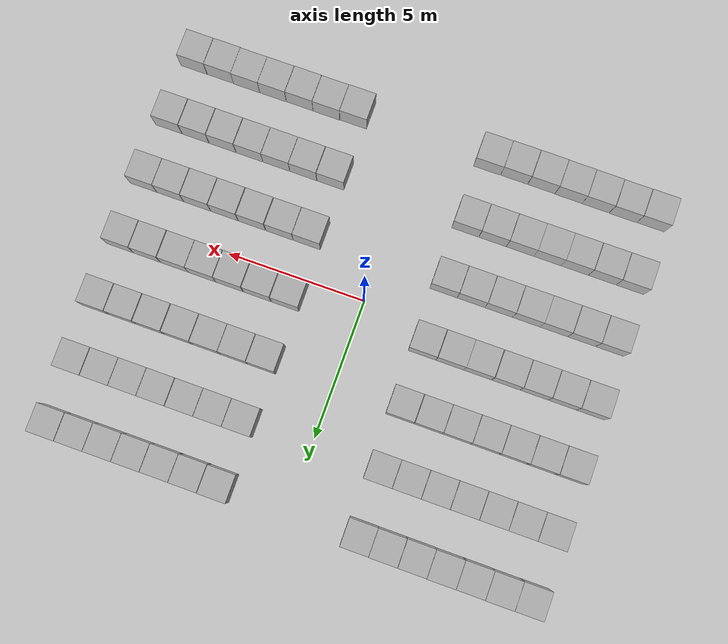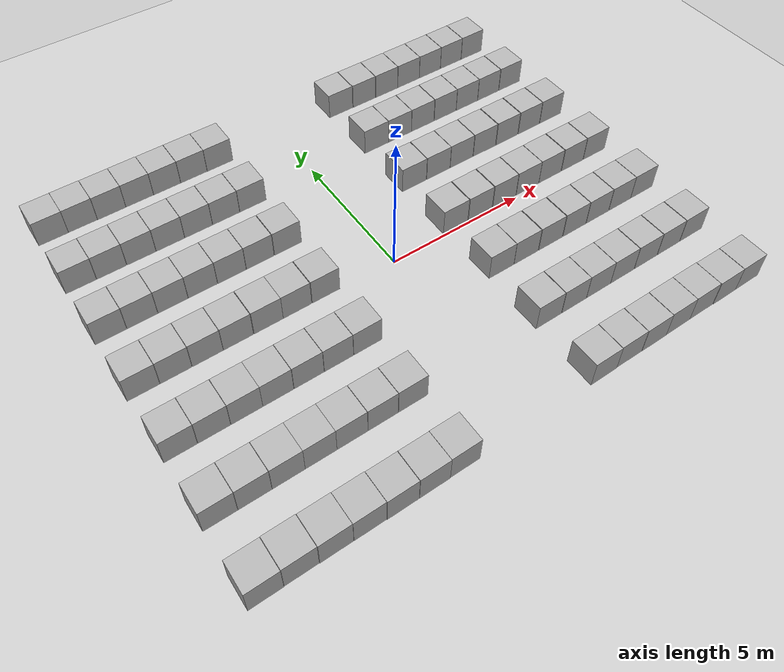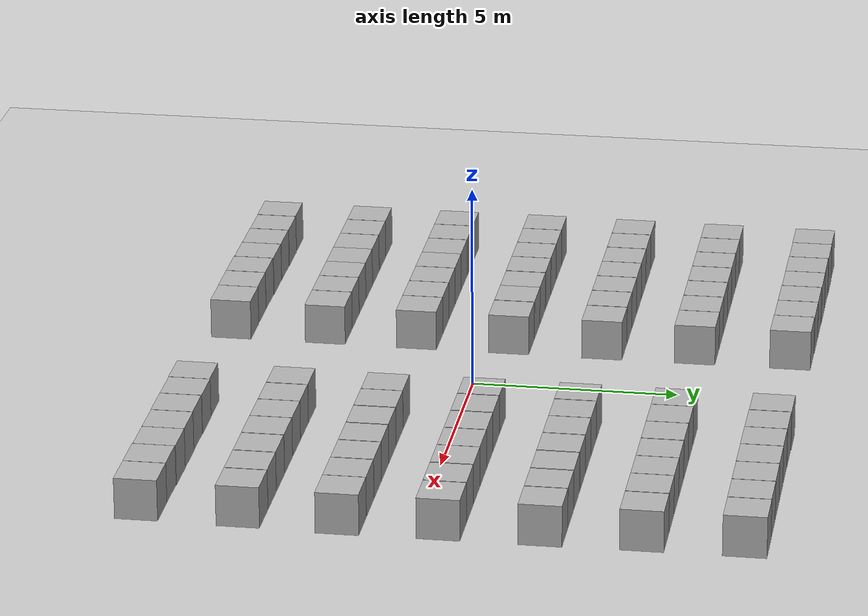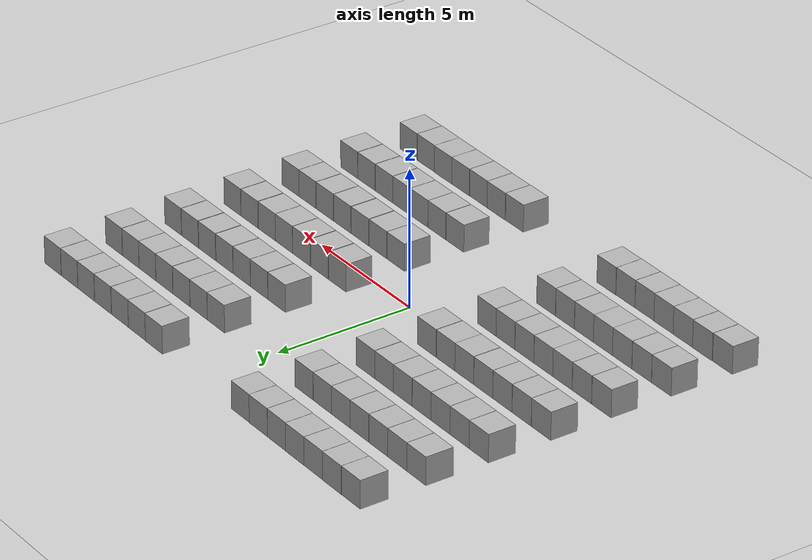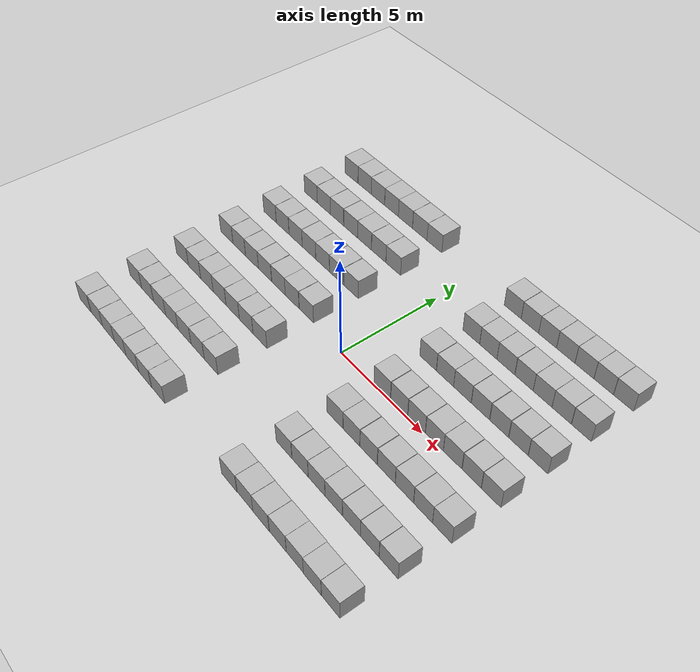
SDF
<sdf version="1.10">
 <world name="empty">
  <physics type="ode">
   <max_step_size>0.004</max_step_size>
   <real_time_factor>1.0</real_time_factor>
   <real_time_update_rate>250</real_time_update_rate>
  </physics>
  <plugin name="gz::sim::systems::Physics" filename="ignition-gazebo-physics-system"/>
  <plugin name="gz::sim::systems::UserCommands" filename="ignition-gazebo-user-commands-system"/>
  <plugin name="gz::sim::systems::SceneBroadcaster" filename="ignition-gazebo-scene-broadcaster-system"/>
  <plugin name="gz::sim::systems::Contact" filename="ignition-gazebo-contact-system"/>
  <gravity>0 0 -9.8000000000000007</gravity>
  <magnetic_field>6.0000000000000002e-06 2.3e-05 -4.1999999999999998e-05</magnetic_field>
  <atmosphere type="adiabatic"/>
  <scene>
   <ambient>0.400000006 0.400000006 0.400000006 1</ambient>
   <background>0.699999988 0.699999988 0.699999988 1</background>
   <shadows>true</shadows>
  </scene>
  <model name="ground_plane">
   <static>true</static>
   <link name="link">
    <collision name="collision">
     <geometry><plane><normal>0 0 1</normal><size>100 100</size></plane></geometry>
    </collision>
    <visual name="visual">
     <geometry><plane><normal>0 0 1</normal><size>100 100</size></plane></geometry>
     <material>
      <ambient>0.800000012 0.800000012 0.800000012 1</ambient>
      <diffuse>0.800000012 0.800000012 0.800000012 1</diffuse>
      <specular>0.800000012 0.800000012 0.800000012 1</specular>
     </material>
    </visual>
    <inertial>
     <mass>1</mass>
     <inertia><ixx>1</ixx><ixy>0</ixy><ixz>0</ixz><iyy>1</iyy><iyz>0</iyz><izz>1</izz></inertia>
    </inertial>
   </link>
  </model>
  <model name="box_0">
   <pose>2.5 2.8999999999999999 0.49999999990199806 6.1203827244439096e-21 -3.3876359505899643e-21 1.6466037992492553e-22</pose>
   <link name="box_link">
    <inertial>
     <inertia><ixx>0.16666</ixx><ixy>0</ixy><ixz>0</ixz><iyy>0.16666</iyy><iyz>0</iyz><izz>0.16666</izz></inertia>
     <mass>1</mass>
    </inertial>
    <collision name="box_collision"><geometry><box><size>1 1 1</size></box></geometry></collision>
    <visual name="box_visual">
     <geometry><box><size>1 1 1</size></box></geometry>
     <material>
      <ambient>0.300000012 0.300000012 0.300000012 1</ambient>
      <diffuse>0.699999988 0.699999988 0.699999988 1</diffuse>
      <specular>1 1 1 1</specular>
     </material>
    </visual>
   </link>
   <static>false</static>
  </model>
  <model name="box_1">
   <pose>2.5 0.58999999999999997 0.49999999990199806 8.7066809390667723e-22 -2.1285260495278108e-21 1.1545711030765614e-22</pose>
   <link name="box_link">
    <inertial>
     <inertia><ixx>0.16666</ixx><ixy>0</ixy><ixz>0</ixz><iyy>0.16666</iyy><iyz>0</iyz><izz>0.16666</izz></inertia>
     <mass>1</mass>
    </inertial>
    <collision name="box_collision"><geometry><box><size>1 1 1</size></box></geometry></collision>
    <visual name="box_visual">
     <geometry><box><size>1 1 1</size></box></geometry>
     <material>
      <ambient>0.300000012 0.300000012 0.300000012 1</ambient>
      <diffuse>0.699999988 0.699999988 0.699999988 1</diffuse>
      <specular>1 1 1 1</specular>
     </material>
    </visual>
   </link>
   <static>false</static>
  </model>
  <model name="box_2">
   <pose>3.52 2.8999999999999999 0.49999999990199806 -4.8768695265223027e-21 5.8225065261525486e-22 -7.5141929730115795e-25</pose>
   <link name="box_link">
    <inertial>
     <inertia><ixx>0.16666</ixx><ixy>0</ixy><ixz>0</ixz><iyy>0.16666</iyy><iyz>0</iyz><izz>0.16666</izz></inertia>
     <mass>1</mass>
    </inertial>
    <collision name="box_collision"><geometry><box><size>1 1 1</size></box></geometry></collision>
    <visual name="box_visual">
     <geometry><box><size>1 1 1</size></box></geometry>
     <material>
      <ambient>0.300000012 0.300000012 0.300000012 1</ambient>
      <diffuse>0.699999988 0.699999988 0.699999988 1</diffuse>
      <specular>1 1 1 1</specular>
     </material>
    </visual>
   </link>
   <static>false</static>
  </model>
  <model name="box_2_1">
   <pose>4.5300000000000002 2.8999999999999999 0.49999999990199806 4.2898201230764065e-21 -2.725349153175945e-21 -8.5990281335853726e-23</pose>
   <link name="box_link">
    <inertial>
     <inertia><ixx>0.16666</ixx><ixy>0</ixy><ixz>0</ixz><iyy>0.16666</iyy><iyz>0</iyz><izz>0.16666</izz></inertia>
     <mass>1</mass>
    </inertial>
    <collision name="box_collision"><geometry><box><size>1 1 1</size></box></geometry></collision>
    <visual name="box_visual">
     <geometry><box><size>1 1 1</size></box></geometry>
     <material>
      <ambient>0.300000012 0.300000012 0.300000012 1</ambient>
      <diffuse>0.699999988 0.699999988 0.699999988 1</diffuse>
      <specular>1 1 1 1</specular>
     </material>
    </visual>
   </link>
   <static>false</static>
  </model>
  <model name="box_3">
   <pose>5.5499999999999998 2.8999999999999999 0.49999999990199806 5.2887159057370552e-21 -3.6750628121331441e-21 -3.6849575540852575e-22</pose>
   <link name="box_link">
    <inertial>
     <inertia><ixx>0.16666</ixx><ixy>0</ixy><ixz>0</ixz><iyy>0.16666</iyy><iyz>0</iyz><izz>0.16666</izz></inertia>
     <mass>1</mass>
    </inertial>
    <collision name="box_collision"><geometry><box><size>1 1 1</size></box></geometry></collision>
    <visual name="box_visual">
     <geometry><box><size>1 1 1</size></box></geometry>
     <material>
      <ambient>0.300000012 0.300000012 0.300000012 1</ambient>
      <diffuse>0.699999988 0.699999988 0.699999988 1</diffuse>
      <specular>1 1 1 1</specular>
     </material>
    </visual>
   </link>
   <static>false</static>
  </model>
  <model name="box_4">
   <pose>6.5800000000000001 2.8999999999999999 0.49999999990199806 -2.4660929546317553e-21 -9.2821509608650037e-21 -8.2239956414060735e-22</pose>
   <link name="box_link">
    <inertial>
     <inertia><ixx>0.16666</ixx><ixy>0</ixy><ixz>0</ixz><iyy>0.16666</iyy><iyz>0</iyz><izz>0.16666</izz></inertia>
     <mass>1</mass>
    </inertial>
    <collision name="box_collision"><geometry><box><size>1 1 1</size></box></geometry></collision>
    <visual name="box_visual">
     <geometry><box><size>1 1 1</size></box></geometry>
     <material>
      <ambient>0.300000012 0.300000012 0.300000012 1</ambient>
      <diffuse>0.699999988 0.699999988 0.699999988 1</diffuse>
      <specular>1 1 1 1</specular>
     </material>
    </visual>
   </link>
   <static>false</static>
  </model>
  <model name="box_5">
   <pose>7.6100000000000003 2.8999999999999999 0.49999999990199806 2.6876898212229476e-22 -1.2926105225332566e-21 -3.0142882185984917e-22</pose>
   <link name="box_link">
    <inertial>
     <inertia><ixx>0.16666</ixx><ixy>0</ixy><ixz>0</ixz><iyy>0.16666</iyy><iyz>0</iyz><izz>0.16666</izz></inertia>
     <mass>1</mass>
    </inertial>
    <collision name="box_collision"><geometry><box><size>1 1 1</size></box></geometry></collision>
    <visual name="box_visual">
     <geometry><box><size>1 1 1</size></box></geometry>
     <material>
      <ambient>0.300000012 0.300000012 0.300000012 1</ambient>
      <diffuse>0.699999988 0.699999988 0.699999988 1</diffuse>
      <specular>1 1 1 1</specular>
     </material>
    </visual>
   </link>
   <static>false</static>
  </model>
  <model name="box_6">
   <pose>8.6300000000000008 2.8999999999999999 0.49999999990199806 1.9043130121824857e-21 8.8559634418370129e-21 -4.3486632422214666e-23</pose>
   <link name="box_link">
    <inertial>
     <inertia><ixx>0.16666</ixx><ixy>0</ixy><ixz>0</ixz><iyy>0.16666</iyy><iyz>0</iyz><izz>0.16666</izz></inertia>
     <mass>1</mass>
    </inertial>
    <collision name="box_collision"><geometry><box><size>1 1 1</size></box></geometry></collision>
    <visual name="box_visual">
     <geometry><box><size>1 1 1</size></box></geometry>
     <material>
      <ambient>0.300000012 0.300000012 0.300000012 1</ambient>
      <diffuse>0.699999988 0.699999988 0.699999988 1</diffuse>
      <specular>1 1 1 1</specular>
     </material>
    </visual>
   </link>
   <static>false</static>
  </model>
  <model name="box_7">
   <pose>3.5299999999999998 0.58999999999999986 0.49999999990199806 -9.9876155932578515e-22 -3.3279681376680838e-21 1.0376628418611865e-22</pose>
   <link name="box_link">
    <inertial>
     <inertia><ixx>0.16666</ixx><ixy>0</ixy><ixz>0</ixz><iyy>0.16666</iyy><iyz>0</iyz><izz>0.16666</izz></inertia>
     <mass>1</mass>
    </inertial>
    <collision name="box_collision"><geometry><box><size>1 1 1</size></box></geometry></collision>
    <visual name="box_visual">
     <geometry><box><size>1 1 1</size></box></geometry>
     <material>
      <ambient>0.300000012 0.300000012 0.300000012 1</ambient>
      <diffuse>0.699999988 0.699999988 0.699999988 1</diffuse>
      <specular>1 1 1 1</specular>
     </material>
    </visual>
   </link>
   <static>false</static>
  </model>
  <model name="box_8">
   <pose>4.5599999999999996 0.58999999999999986 0.49999999990199806 8.0483898771128715e-22 -1.9664387365039291e-21 2.629122359092698e-22</pose>
   <link name="box_link">
    <inertial>
     <inertia><ixx>0.16666</ixx><ixy>0</ixy><ixz>0</ixz><iyy>0.16666</iyy><iyz>0</iyz><izz>0.16666</izz></inertia>
     <mass>1</mass>
    </inertial>
    <collision name="box_collision"><geometry><box><size>1 1 1</size></box></geometry></collision>
    <visual name="box_visual">
     <geometry><box><size>1 1 1</size></box></geometry>
     <material>
      <ambient>0.300000012 0.300000012 0.300000012 1</ambient>
      <diffuse>0.699999988 0.699999988 0.699999988 1</diffuse>
      <specular>1 1 1 1</specular>
     </material>
    </visual>
   </link>
   <static>false</static>
  </model>
  <model name="box_9">
   <pose>5.5800000000000001 0.59000000000000008 0.49999999990199806 -3.7574526127707067e-21 -2.7620760771008262e-21 -5.0334515553601907e-22</pose>
   <link name="box_link">
    <inertial>
     <inertia><ixx>0.16666</ixx><ixy>0</ixy><ixz>0</ixz><iyy>0.16666</iyy><iyz>0</iyz><izz>0.16666</izz></inertia>
     <mass>1</mass>
    </inertial>
    <collision name="box_collision"><geometry><box><size>1 1 1</size></box></geometry></collision>
    <visual name="box_visual">
     <geometry><box><size>1 1 1</size></box></geometry>
     <material>
      <ambient>0.300000012 0.300000012 0.300000012 1</ambient>
      <diffuse>0.699999988 0.699999988 0.699999988 1</diffuse>
      <specular>1 1 1 1</specular>
     </material>
    </visual>
   </link>
   <static>false</static>
  </model>
  <model name="box_10">
   <pose>6.5899999999999999 0.58999999999999986 0.49999999990199806 1.8321338117819254e-21 -8.3511235812931385e-22 -1.072067985728647e-22</pose>
   <link name="box_link">
    <inertial>
     <inertia><ixx>0.16666</ixx><ixy>0</ixy><ixz>0</ixz><iyy>0.16666</iyy><iyz>0</iyz><izz>0.16666</izz></inertia>
     <mass>1</mass>
    </inertial>
    <collision name="box_collision"><geometry><box><size>1 1 1</size></box></geometry></collision>
    <visual name="box_visual">
     <geometry><box><size>1 1 1</size></box></geometry>
     <material>
      <ambient>0.300000012 0.300000012 0.300000012 1</ambient>
      <diffuse>0.699999988 0.699999988 0.699999988 1</diffuse>
      <specular>1 1 1 1</specular>
     </material>
    </visual>
   </link>
   <static>false</static>
  </model>
  <model name="box_11">
   <pose>7.6200000000000001 0.58999999999999986 0.49999999990199806 -9.8022300570000345e-22 -1.2140919249779047e-21 -6.2576101818199715e-22</pose>
   <link name="box_link">
    <inertial>
     <inertia><ixx>0.16666</ixx><ixy>0</ixy><ixz>0</ixz><iyy>0.16666</iyy><iyz>0</iyz><izz>0.16666</izz></inertia>
     <mass>1</mass>
    </inertial>
    <collision name="box_collision"><geometry><box><size>1 1 1</size></box></geometry></collision>
    <visual name="box_visual">
     <geometry><box><size>1 1 1</size></box></geometry>
     <material>
      <ambient>0.300000012 0.300000012 0.300000012 1</ambient>
      <diffuse>0.699999988 0.699999988 0.699999988 1</diffuse>
      <specular>1 1 1 1</specular>
     </material>
    </visual>
   </link>
   <static>false</static>
  </model>
  <model name="box_12">
   <pose>8.6400000000000006 0.58999999999999986 0.49999999990199806 1.1685815462847036e-21 3.8251662251648546e-22 1.9598060917783797e-23</pose>
   <link name="box_link">
    <inertial>
     <inertia><ixx>0.16666</ixx><ixy>0</ixy><ixz>0</ixz><iyy>0.16666</iyy><iyz>0</iyz><izz>0.16666</izz></inertia>
     <mass>1</mass>
    </inertial>
    <collision name="box_collision"><geometry><box><size>1 1 1</size></box></geometry></collision>
    <visual name="box_visual">
     <geometry><box><size>1 1 1</size></box></geometry>
     <material>
      <ambient>0.300000012 0.300000012 0.300000012 1</ambient>
      <diffuse>0.699999988 0.699999988 0.699999988 1</diffuse>
      <specular>1 1 1 1</specular>
     </material>
    </visual>
   </link>
   <static>false</static>
  </model>
  <model name="box_13">
   <pose>2.5499999999999998 -1.71 0.5 1.6937504338995532e-43 0 0</pose>
   <link name="box_link">
    <inertial>
     <inertia><ixx>0.16666</ixx><ixy>0</ixy><ixz>0</ixz><iyy>0.16666</iyy><iyz>0</iyz><izz>0.16666</izz></inertia>
     <mass>1</mass>
    </inertial>
    <collision name="box_collision"><geometry><box><size>1 1 1</size></box></geometry></collision>
    <visual name="box_visual">
     <geometry><box><size>1 1 1</size></box></geometry>
     <material>
      <ambient>0.300000012 0.300000012 0.300000012 1</ambient>
      <diffuse>0.699999988 0.699999988 0.699999988 1</diffuse>
      <specular>1 1 1 1</specular>
     </material>
    </visual>
   </link>
   <static>false</static>
  </model>
  <model name="box_14">
   <pose>3.5600000000000001 -1.71 0.5 1.6937504338995532e-43 0 0</pose>
   <link name="box_link">
    <inertial>
     <inertia><ixx>0.16666</ixx><ixy>0</ixy><ixz>0</ixz><iyy>0.16666</iyy><iyz>0</iyz><izz>0.16666</izz></inertia>
     <mass>1</mass>
    </inertial>
    <collision name="box_collision"><geometry><box><size>1 1 1</size></box></geometry></collision>
    <visual name="box_visual">
     <geometry><box><size>1 1 1</size></box></geometry>
     <material>
      <ambient>0.300000012 0.300000012 0.300000012 1</ambient>
      <diffuse>0.699999988 0.699999988 0.699999988 1</diffuse>
      <specular>1 1 1 1</specular>
     </material>
    </visual>
   </link>
   <static>false</static>
  </model>
  <model name="box_15">
   <pose>4.5899999999999999 -1.71 0.5 1.6937504338995532e-43 0 0</pose>
   <link name="box_link">
    <inertial>
     <inertia><ixx>0.16666</ixx><ixy>0</ixy><ixz>0</ixz><iyy>0.16666</iyy><iyz>0</iyz><izz>0.16666</izz></inertia>
     <mass>1</mass>
    </inertial>
    <collision name="box_collision"><geometry><box><size>1 1 1</size></box></geometry></collision>
    <visual name="box_visual">
     <geometry><box><size>1 1 1</size></box></geometry>
     <material>
      <ambient>0.300000012 0.300000012 0.300000012 1</ambient>
      <diffuse>0.699999988 0.699999988 0.699999988 1</diffuse>
      <specular>1 1 1 1</specular>
     </material>
    </visual>
   </link>
   <static>false</static>
  </model>
  <model name="box_16">
   <pose>5.6200000000000001 -1.71 0.5 1.6937504338995532e-43 0 0</pose>
   <link name="box_link">
    <inertial>
     <inertia><ixx>0.16666</ixx><ixy>0</ixy><ixz>0</ixz><iyy>0.16666</iyy><iyz>0</iyz><izz>0.16666</izz></inertia>
     <mass>1</mass>
    </inertial>
    <collision name="box_collision"><geometry><box><size>1 1 1</size></box></geometry></collision>
    <visual name="box_visual">
     <geometry><box><size>1 1 1</size></box></geometry>
     <material>
      <ambient>0.300000012 0.300000012 0.300000012 1</ambient>
      <diffuse>0.699999988 0.699999988 0.699999988 1</diffuse>
      <specular>1 1 1 1</specular>
     </material>
    </visual>
   </link>
   <static>false</static>
  </model>
  <model name="box_17">
   <pose>6.6399999999999997 -1.71 0.5 1.6937504338995532e-43 0 0</pose>
   <link name="box_link">
    <inertial>
     <inertia><ixx>0.16666</ixx><ixy>0</ixy><ixz>0</ixz><iyy>0.16666</iyy><iyz>0</iyz><izz>0.16666</izz></inertia>
     <mass>1</mass>
    </inertial>
    <collision name="box_collision"><geometry><box><size>1 1 1</size></box></geometry></collision>
    <visual name="box_visual">
     <geometry><box><size>1 1 1</size></box></geometry>
     <material>
      <ambient>0.300000012 0.300000012 0.300000012 1</ambient>
      <diffuse>0.699999988 0.699999988 0.699999988 1</diffuse>
      <specular>1 1 1 1</specular>
     </material>
    </visual>
   </link>
   <static>false</static>
  </model>
  <model name="box_18">
   <pose>7.6600000000000001 -1.71 0.5 3.1892209020670102e-43 0 0</pose>
   <link name="box_link">
    <inertial>
     <inertia><ixx>0.16666</ixx><ixy>0</ixy><ixz>0</ixz><iyy>0.16666</iyy><iyz>0</iyz><izz>0.16666</izz></inertia>
     <mass>1</mass>
    </inertial>
    <collision name="box_collision"><geometry><box><size>1 1 1</size></box></geometry></collision>
    <visual name="box_visual">
     <geometry><box><size>1 1 1</size></box></geometry>
     <material>
      <ambient>0.300000012 0.300000012 0.300000012 1</ambient>
      <diffuse>0.699999988 0.699999988 0.699999988 1</diffuse>
      <specular>1 1 1 1</specular>
     </material>
    </visual>
   </link>
   <static>false</static>
  </model>
  <model name="box_19">
   <pose>8.6699999999999999 -1.71 0.5 1.6937504338995532e-43 0 0</pose>
   <link name="box_link">
    <inertial>
     <inertia><ixx>0.16666</ixx><ixy>0</ixy><ixz>0</ixz><iyy>0.16666</iyy><iyz>0</iyz><izz>0.16666</izz></inertia>
     <mass>1</mass>
    </inertial>
    <collision name="box_collision"><geometry><box><size>1 1 1</size></box></geometry></collision>
    <visual name="box_visual">
     <geometry><box><size>1 1 1</size></box></geometry>
     <material>
      <ambient>0.300000012 0.300000012 0.300000012 1</ambient>
      <diffuse>0.699999988 0.699999988 0.699999988 1</diffuse>
      <specular>1 1 1 1</specular>
     </material>
    </visual>
   </link>
   <static>false</static>
  </model>
  <model name="box_20">
   <pose>2.5 -4 0.5 -4.0097937125292166e-44 0 0</pose>
   <link name="box_link">
    <inertial>
     <inertia><ixx>0.16666</ixx><ixy>0</ixy><ixz>0</ixz><iyy>0.16666</iyy><iyz>0</iyz><izz>0.16666</izz></inertia>
     <mass>1</mass>
    </inertial>
    <collision name="box_collision"><geometry><box><size>1 1 1</size></box></geometry></collision>
    <visual name="box_visual">
     <geometry><box><size>1 1 1</size></box></geometry>
     <material>
      <ambient>0.300000012 0.300000012 0.300000012 1</ambient>
      <diffuse>0.699999988 0.699999988 0.699999988 1</diffuse>
      <specular>1 1 1 1</specular>
     </material>
    </visual>
   </link>
   <static>false</static>
  </model>
  <model name="box_21">
   <pose>3.52 -4 0.5 1.6937504338995532e-43 0 0</pose>
   <link name="box_link">
    <inertial>
     <inertia><ixx>0.16666</ixx><ixy>0</ixy><ixz>0</ixz><iyy>0.16666</iyy><iyz>0</iyz><izz>0.16666</izz></inertia>
     <mass>1</mass>
    </inertial>
    <collision name="box_collision"><geometry><box><size>1 1 1</size></box></geometry></collision>
    <visual name="box_visual">
     <geometry><box><size>1 1 1</size></box></geometry>
     <material>
      <ambient>0.300000012 0.300000012 0.300000012 1</ambient>
      <diffuse>0.699999988 0.699999988 0.699999988 1</diffuse>
      <specular>1 1 1 1</specular>
     </material>
    </visual>
   </link>
   <static>false</static>
  </model>
  <model name="box_22">
   <pose>4.5300000000000002 -4 0.5 1.6937504338995532e-43 0 0</pose>
   <link name="box_link">
    <inertial>
     <inertia><ixx>0.16666</ixx><ixy>0</ixy><ixz>0</ixz><iyy>0.16666</iyy><iyz>0</iyz><izz>0.16666</izz></inertia>
     <mass>1</mass>
    </inertial>
    <collision name="box_collision"><geometry><box><size>1 1 1</size></box></geometry></collision>
    <visual name="box_visual">
     <geometry><box><size>1 1 1</size></box></geometry>
     <material>
      <ambient>0.300000012 0.300000012 0.300000012 1</ambient>
      <diffuse>0.699999988 0.699999988 0.699999988 1</diffuse>
      <specular>1 1 1 1</specular>
     </material>
    </visual>
   </link>
   <static>false</static>
  </model>
  <model name="box_23">
   <pose>5.54 -4 0.5 -4.0097937125292166e-44 0 0</pose>
   <link name="box_link">
    <inertial>
     <inertia><ixx>0.16666</ixx><ixy>0</ixy><ixz>0</ixz><iyy>0.16666</iyy><iyz>0</iyz><izz>0.16666</izz></inertia>
     <mass>1</mass>
    </inertial>
    <collision name="box_collision"><geometry><box><size>1 1 1</size></box></geometry></collision>
    <visual name="box_visual">
     <geometry><box><size>1 1 1</size></box></geometry>
     <material>
      <ambient>0.300000012 0.300000012 0.300000012 1</ambient>
      <diffuse>0.699999988 0.699999988 0.699999988 1</diffuse>
      <specular>1 1 1 1</specular>
     </material>
    </visual>
   </link>
   <static>false</static>
  </model>
  <model name="box_24">
   <pose>6.5599999999999996 -4 0.5 5.5058610233241208e-44 0 0</pose>
   <link name="box_link">
    <inertial>
     <inertia><ixx>0.16666</ixx><ixy>0</ixy><ixz>0</ixz><iyy>0.16666</iyy><iyz>0</iyz><izz>0.16666</izz></inertia>
     <mass>1</mass>
    </inertial>
    <collision name="box_collision"><geometry><box><size>1 1 1</size></box></geometry></collision>
    <visual name="box_visual">
     <geometry><box><size>1 1 1</size></box></geometry>
     <material>
      <ambient>0.300000012 0.300000012 0.300000012 1</ambient>
      <diffuse>0.699999988 0.699999988 0.699999988 1</diffuse>
      <specular>1 1 1 1</specular>
     </material>
    </visual>
   </link>
   <static>false</static>
  </model>
  <model name="box_25">
   <pose>7.5800000000000001 -4 0.5 0 0 0</pose>
   <link name="box_link">
    <inertial>
     <inertia><ixx>0.16666</ixx><ixy>0</ixy><ixz>0</ixz><iyy>0.16666</iyy><iyz>0</iyz><izz>0.16666</izz></inertia>
     <mass>1</mass>
    </inertial>
    <collision name="box_collision"><geometry><box><size>1 1 1</size></box></geometry></collision>
    <visual name="box_visual">
     <geometry><box><size>1 1 1</size></box></geometry>
     <material>
      <ambient>0.300000012 0.300000012 0.300000012 1</ambient>
      <diffuse>0.699999988 0.699999988 0.699999988 1</diffuse>
      <specular>1 1 1 1</specular>
     </material>
    </visual>
   </link>
   <static>false</static>
  </model>
  <model name="box_26">
   <pose>8.5999999999999996 -4 0.5 1.6937504338995532e-43 0 0</pose>
   <link name="box_link">
    <inertial>
     <inertia><ixx>0.16666</ixx><ixy>0</ixy><ixz>0</ixz><iyy>0.16666</iyy><iyz>0</iyz><izz>0.16666</izz></inertia>
     <mass>1</mass>
    </inertial>
    <collision name="box_collision"><geometry><box><size>1 1 1</size></box></geometry></collision>
    <visual name="box_visual">
     <geometry><box><size>1 1 1</size></box></geometry>
     <material>
      <ambient>0.300000012 0.300000012 0.300000012 1</ambient>
      <diffuse>0.699999988 0.699999988 0.699999988 1</diffuse>
      <specular>1 1 1 1</specular>
     </material>
    </visual>
   </link>
   <static>false</static>
  </model>
  <model name="box_27">
   <pose>2.5 5.1900000000000004 0.49999999990199806 1.1969889062632419e-21 -2.3994643682355624e-21 -2.0346020328214015e-22</pose>
   <link name="box_link">
    <inertial>
     <inertia><ixx>0.16666</ixx><ixy>0</ixy><ixz>0</ixz><iyy>0.16666</iyy><iyz>0</iyz><izz>0.16666</izz></inertia>
     <mass>1</mass>
    </inertial>
    <collision name="box_collision"><geometry><box><size>1 1 1</size></box></geometry></collision>
    <visual name="box_visual">
     <geometry><box><size>1 1 1</size></box></geometry>
     <material>
      <ambient>0.300000012 0.300000012 0.300000012 1</ambient>
      <diffuse>0.699999988 0.699999988 0.699999988 1</diffuse>
      <specular>1 1 1 1</specular>
     </material>
    </visual>
   </link>
   <static>false</static>
  </model>
  <model name="box_28">
   <pose>3.5099999999999998 5.1900000000000004 0.49999999990199806 2.2166818924739801e-21 -3.9964851649350918e-21 -2.8454415990004946e-22</pose>
   <link name="box_link">
    <inertial>
     <inertia><ixx>0.16666</ixx><ixy>0</ixy><ixz>0</ixz><iyy>0.16666</iyy><iyz>0</iyz><izz>0.16666</izz></inertia>
     <mass>1</mass>
    </inertial>
    <collision name="box_collision"><geometry><box><size>1 1 1</size></box></geometry></collision>
    <visual name="box_visual">
     <geometry><box><size>1 1 1</size></box></geometry>
     <material>
      <ambient>0.300000012 0.300000012 0.300000012 1</ambient>
      <diffuse>0.699999988 0.699999988 0.699999988 1</diffuse>
      <specular>1 1 1 1</specular>
     </material>
    </visual>
   </link>
   <static>false</static>
  </model>
  <model name="box_29">
   <pose>4.5199999999999996 5.1900000000000004 0.49999999990199806 1.9003650826657693e-21 -3.9955080593532145e-21 -2.0083520017725128e-22</pose>
   <link name="box_link">
    <inertial>
     <inertia><ixx>0.16666</ixx><ixy>0</ixy><ixz>0</ixz><iyy>0.16666</iyy><iyz>0</iyz><izz>0.16666</izz></inertia>
     <mass>1</mass>
    </inertial>
    <collision name="box_collision"><geometry><box><size>1 1 1</size></box></geometry></collision>
    <visual name="box_visual">
     <geometry><box><size>1 1 1</size></box></geometry>
     <material>
      <ambient>0.300000012 0.300000012 0.300000012 1</ambient>
      <diffuse>0.699999988 0.699999988 0.699999988 1</diffuse>
      <specular>1 1 1 1</specular>
     </material>
    </visual>
   </link>
   <static>false</static>
  </model>
  <model name="box_30">
   <pose>5.54 5.1900000000000004 0.49999999990199806 5.9551544824185483e-22 -2.0198700582976372e-21 1.1317465050277089e-22</pose>
   <link name="box_link">
    <inertial>
     <inertia><ixx>0.16666</ixx><ixy>0</ixy><ixz>0</ixz><iyy>0.16666</iyy><iyz>0</iyz><izz>0.16666</izz></inertia>
     <mass>1</mass>
    </inertial>
    <collision name="box_collision"><geometry><box><size>1 1 1</size></box></geometry></collision>
    <visual name="box_visual">
     <geometry><box><size>1 1 1</size></box></geometry>
     <material>
      <ambient>0.300000012 0.300000012 0.300000012 1</ambient>
      <diffuse>0.699999988 0.699999988 0.699999988 1</diffuse>
      <specular>1 1 1 1</specular>
     </material>
    </visual>
   </link>
   <static>false</static>
  </model>
  <model name="box_31">
   <pose>6.5499999999999998 5.1900000000000004 0.49999999990199806 4.1068825242664722e-21 -4.6250560261045752e-21 -1.0639733848401009e-22</pose>
   <link name="box_link">
    <inertial>
     <inertia><ixx>0.16666</ixx><ixy>0</ixy><ixz>0</ixz><iyy>0.16666</iyy><iyz>0</iyz><izz>0.16666</izz></inertia>
     <mass>1</mass>
    </inertial>
    <collision name="box_collision"><geometry><box><size>1 1 1</size></box></geometry></collision>
    <visual name="box_visual">
     <geometry><box><size>1 1 1</size></box></geometry>
     <material>
      <ambient>0.300000012 0.300000012 0.300000012 1</ambient>
      <diffuse>0.699999988 0.699999988 0.699999988 1</diffuse>
      <specular>1 1 1 1</specular>
     </material>
    </visual>
   </link>
   <static>false</static>
  </model>
  <model name="box_32">
   <pose>7.5599999999999996 5.1900000000000004 0.49999999990199806 1.1033215412143612e-21 -1.9986045541170091e-21 1.2186978225147396e-22</pose>
   <link name="box_link">
    <inertial>
     <inertia><ixx>0.16666</ixx><ixy>0</ixy><ixz>0</ixz><iyy>0.16666</iyy><iyz>0</iyz><izz>0.16666</izz></inertia>
     <mass>1</mass>
    </inertial>
    <collision name="box_collision"><geometry><box><size>1 1 1</size></box></geometry></collision>
    <visual name="box_visual">
     <geometry><box><size>1 1 1</size></box></geometry>
     <material>
      <ambient>0.300000012 0.300000012 0.300000012 1</ambient>
      <diffuse>0.699999988 0.699999988 0.699999988 1</diffuse>
      <specular>1 1 1 1</specular>
     </material>
    </visual>
   </link>
   <static>false</static>
  </model>
  <model name="box_33">
   <pose>8.5800000000000001 5.1900000000000004 0.49999999990199806 1.238854400850552e-21 -4.5157620254319641e-21 -3.3539173515085679e-22</pose>
   <link name="box_link">
    <inertial>
     <inertia><ixx>0.16666</ixx><ixy>0</ixy><ixz>0</ixz><iyy>0.16666</iyy><iyz>0</iyz><izz>0.16666</izz></inertia>
     <mass>1</mass>
    </inertial>
    <collision name="box_collision"><geometry><box><size>1 1 1</size></box></geometry></collision>
    <visual name="box_visual">
     <geometry><box><size>1 1 1</size></box></geometry>
     <material>
      <ambient>0.300000012 0.300000012 0.300000012 1</ambient>
      <diffuse>0.699999988 0.699999988 0.699999988 1</diffuse>
      <specular>1 1 1 1</specular>
     </material>
    </visual>
   </link>
   <static>false</static>
  </model>
  <model name="box_34">
   <pose>2.4910600000000001 7.50007 0.49999999990199806 -2.5397393684422978e-21 1.8424908735395696e-21 -3.4618579833306759e-22</pose>
   <link name="box_link">
    <inertial>
     <inertia><ixx>0.16666</ixx><ixy>0</ixy><ixz>0</ixz><iyy>0.16666</iyy><iyz>0</iyz><izz>0.16666</izz></inertia>
     <mass>1</mass>
    </inertial>
    <collision name="box_collision"><geometry><box><size>1 1 1</size></box></geometry></collision>
    <visual name="box_visual">
     <geometry><box><size>1 1 1</size></box></geometry>
     <material>
      <ambient>0.300000012 0.300000012 0.300000012 1</ambient>
      <diffuse>0.699999988 0.699999988 0.699999988 1</diffuse>
      <specular>1 1 1 1</specular>
     </material>
    </visual>
   </link>
   <static>false</static>
  </model>
  <model name="box_35">
   <pose>3.5087299999999999 7.4916299999999998 0.49999999990199806 6.2287739151293738e-22 9.3279666454713669e-22 -3.6315533669320137e-22</pose>
   <link name="box_link">
    <inertial>
     <inertia><ixx>0.16666</ixx><ixy>0</ixy><ixz>0</ixz><iyy>0.16666</iyy><iyz>0</iyz><izz>0.16666</izz></inertia>
     <mass>1</mass>
    </inertial>
    <collision name="box_collision"><geometry><box><size>1 1 1</size></box></geometry></collision>
    <visual name="box_visual">
     <geometry><box><size>1 1 1</size></box></geometry>
     <material>
      <ambient>0.300000012 0.300000012 0.300000012 1</ambient>
      <diffuse>0.699999988 0.699999988 0.699999988 1</diffuse>
      <specular>1 1 1 1</specular>
     </material>
    </visual>
   </link>
   <static>false</static>
  </model>
  <model name="box_36">
   <pose>4.5188100000000002 7.4887300000000003 0.49999999990199806 6.2287739151293738e-22 9.3279666454713669e-22 -3.6315533669320137e-22</pose>
   <link name="box_link">
    <inertial>
     <inertia><ixx>0.16666</ixx><ixy>0</ixy><ixz>0</ixz><iyy>0.16666</iyy><iyz>0</iyz><izz>0.16666</izz></inertia>
     <mass>1</mass>
    </inertial>
    <collision name="box_collision"><geometry><box><size>1 1 1</size></box></geometry></collision>
    <visual name="box_visual">
     <geometry><box><size>1 1 1</size></box></geometry>
     <material>
      <ambient>0.300000012 0.300000012 0.300000012 1</ambient>
      <diffuse>0.699999988 0.699999988 0.699999988 1</diffuse>
      <specular>1 1 1 1</specular>
     </material>
    </visual>
   </link>
   <static>false</static>
  </model>
  <model name="box_37">
   <pose>5.5303100000000001 7.4918100000000001 0.49999999990199806 6.2287739151293738e-22 9.3279666454713669e-22 -3.6315533669320137e-22</pose>
   <link name="box_link">
    <inertial>
     <inertia><ixx>0.16666</ixx><ixy>0</ixy><ixz>0</ixz><iyy>0.16666</iyy><iyz>0</iyz><izz>0.16666</izz></inertia>
     <mass>1</mass>
    </inertial>
    <collision name="box_collision"><geometry><box><size>1 1 1</size></box></geometry></collision>
    <visual name="box_visual">
     <geometry><box><size>1 1 1</size></box></geometry>
     <material>
      <ambient>0.300000012 0.300000012 0.300000012 1</ambient>
      <diffuse>0.699999988 0.699999988 0.699999988 1</diffuse>
      <specular>1 1 1 1</specular>
     </material>
    </visual>
   </link>
   <static>false</static>
  </model>
  <model name="box_38">
   <pose>6.5403799999999999 7.4937399999999998 0.49999999990199806 6.2287739151293738e-22 9.3279666454713669e-22 -3.6315533669320137e-22</pose>
   <link name="box_link">
    <inertial>
     <inertia><ixx>0.16666</ixx><ixy>0</ixy><ixz>0</ixz><iyy>0.16666</iyy><iyz>0</iyz><izz>0.16666</izz></inertia>
     <mass>1</mass>
    </inertial>
    <collision name="box_collision"><geometry><box><size>1 1 1</size></box></geometry></collision>
    <visual name="box_visual">
     <geometry><box><size>1 1 1</size></box></geometry>
     <material>
      <ambient>0.300000012 0.300000012 0.300000012 1</ambient>
      <diffuse>0.699999988 0.699999988 0.699999988 1</diffuse>
      <specular>1 1 1 1</specular>
     </material>
    </visual>
   </link>
   <static>false</static>
  </model>
  <model name="box_39">
   <pose>7.5513199999999996 7.4974400000000001 0.49999999990199806 -2.5397394976504581e-21 1.8424908921771544e-21 -3.4618579832419256e-22</pose>
   <link name="box_link">
    <inertial>
     <inertia><ixx>0.16666</ixx><ixy>0</ixy><ixz>0</ixz><iyy>0.16666</iyy><iyz>0</iyz><izz>0.16666</izz></inertia>
     <mass>1</mass>
    </inertial>
    <collision name="box_collision"><geometry><box><size>1 1 1</size></box></geometry></collision>
    <visual name="box_visual">
     <geometry><box><size>1 1 1</size></box></geometry>
     <material>
      <ambient>0.300000012 0.300000012 0.300000012 1</ambient>
      <diffuse>0.699999988 0.699999988 0.699999988 1</diffuse>
      <specular>1 1 1 1</specular>
     </material>
    </visual>
   </link>
   <static>false</static>
  </model>
  <model name="box_40">
   <pose>8.5660299999999996 7.50075 0.49999999990199806 6.2287739151293738e-22 9.3279666454713669e-22 -3.6315533669320137e-22</pose>
   <link name="box_link">
    <inertial>
     <inertia><ixx>0.16666</ixx><ixy>0</ixy><ixz>0</ixz><iyy>0.16666</iyy><iyz>0</iyz><izz>0.16666</izz></inertia>
     <mass>1</mass>
    </inertial>
    <collision name="box_collision"><geometry><box><size>1 1 1</size></box></geometry></collision>
    <visual name="box_visual">
     <geometry><box><size>1 1 1</size></box></geometry>
     <material>
      <ambient>0.300000012 0.300000012 0.300000012 1</ambient>
      <diffuse>0.699999988 0.699999988 0.699999988 1</diffuse>
      <specular>1 1 1 1</specular>
     </material>
    </visual>
   </link>
   <static>false</static>
  </model>
  <model name="box_41">
   <pose>-2.4900000000000002 -1.71 0.5 1.6937504338995532e-43 0 0</pose>
   <link name="box_link">
    <inertial>
     <inertia><ixx>0.16666</ixx><ixy>0</ixy><ixz>0</ixz><iyy>0.16666</iyy><iyz>0</iyz><izz>0.16666</izz></inertia>
     <mass>1</mass>
    </inertial>
    <collision name="box_collision"><geometry><box><size>1 1 1</size></box></geometry></collision>
    <visual name="box_visual">
     <geometry><box><size>1 1 1</size></box></geometry>
     <material>
      <ambient>0.300000012 0.300000012 0.300000012 1</ambient>
      <diffuse>0.699999988 0.699999988 0.699999988 1</diffuse>
      <specular>1 1 1 1</specular>
     </material>
    </visual>
   </link>
   <static>false</static>
  </model>
  <model name="box_42">
   <pose>-3.5 -1.71 0.5 1.6937504338995532e-43 0 0</pose>
   <link name="box_link">
    <inertial>
     <inertia><ixx>0.16666</ixx><ixy>0</ixy><ixz>0</ixz><iyy>0.16666</iyy><iyz>0</iyz><izz>0.16666</izz></inertia>
     <mass>1</mass>
    </inertial>
    <collision name="box_collision"><geometry><box><size>1 1 1</size></box></geometry></collision>
    <visual name="box_visual">
     <geometry><box><size>1 1 1</size></box></geometry>
     <material>
      <ambient>0.300000012 0.300000012 0.300000012 1</ambient>
      <diffuse>0.699999988 0.699999988 0.699999988 1</diffuse>
      <specular>1 1 1 1</specular>
     </material>
    </visual>
   </link>
   <static>false</static>
  </model>
  <model name="box_43">
   <pose>-4.5099999999999998 -1.71 0.5 1.6937504338995532e-43 0 0</pose>
   <link name="box_link">
    <inertial>
     <inertia><ixx>0.16666</ixx><ixy>0</ixy><ixz>0</ixz><iyy>0.16666</iyy><iyz>0</iyz><izz>0.16666</izz></inertia>
     <mass>1</mass>
    </inertial>
    <collision name="box_collision"><geometry><box><size>1 1 1</size></box></geometry></collision>
    <visual name="box_visual">
     <geometry><box><size>1 1 1</size></box></geometry>
     <material>
      <ambient>0.300000012 0.300000012 0.300000012 1</ambient>
      <diffuse>0.699999988 0.699999988 0.699999988 1</diffuse>
      <specular>1 1 1 1</specular>
     </material>
    </visual>
   </link>
   <static>false</static>
  </model>
  <model name="box_44">
   <pose>-5.5199999999999996 -1.71 0.5 1.6937504338995532e-43 0 0</pose>
   <link name="box_link">
    <inertial>
     <inertia><ixx>0.16666</ixx><ixy>0</ixy><ixz>0</ixz><iyy>0.16666</iyy><iyz>0</iyz><izz>0.16666</izz></inertia>
     <mass>1</mass>
    </inertial>
    <collision name="box_collision"><geometry><box><size>1 1 1</size></box></geometry></collision>
    <visual name="box_visual">
     <geometry><box><size>1 1 1</size></box></geometry>
     <material>
      <ambient>0.300000012 0.300000012 0.300000012 1</ambient>
      <diffuse>0.699999988 0.699999988 0.699999988 1</diffuse>
      <specular>1 1 1 1</specular>
     </material>
    </visual>
   </link>
   <static>false</static>
  </model>
  <model name="box_45">
   <pose>-6.5199999999999996 -1.71 0.5 1.6937504338995532e-43 0 0</pose>
   <link name="box_link">
    <inertial>
     <inertia><ixx>0.16666</ixx><ixy>0</ixy><ixz>0</ixz><iyy>0.16666</iyy><iyz>0</iyz><izz>0.16666</izz></inertia>
     <mass>1</mass>
    </inertial>
    <collision name="box_collision"><geometry><box><size>1 1 1</size></box></geometry></collision>
    <visual name="box_visual">
     <geometry><box><size>1 1 1</size></box></geometry>
     <material>
      <ambient>0.300000012 0.300000012 0.300000012 1</ambient>
      <diffuse>0.699999988 0.699999988 0.699999988 1</diffuse>
      <specular>1 1 1 1</specular>
     </material>
    </visual>
   </link>
   <static>false</static>
  </model>
  <model name="box_46">
   <pose>-7.5300000000000002 -1.71 0.5 1.6937504338995532e-43 0 0</pose>
   <link name="box_link">
    <inertial>
     <inertia><ixx>0.16666</ixx><ixy>0</ixy><ixz>0</ixz><iyy>0.16666</iyy><iyz>0</iyz><izz>0.16666</izz></inertia>
     <mass>1</mass>
    </inertial>
    <collision name="box_collision"><geometry><box><size>1 1 1</size></box></geometry></collision>
    <visual name="box_visual">
     <geometry><box><size>1 1 1</size></box></geometry>
     <material>
      <ambient>0.300000012 0.300000012 0.300000012 1</ambient>
      <diffuse>0.699999988 0.699999988 0.699999988 1</diffuse>
      <specular>1 1 1 1</specular>
     </material>
    </visual>
   </link>
   <static>false</static>
  </model>
  <model name="box_47">
   <pose>-8.5399999999999991 -1.71 0.5 1.6937504338995532e-43 0 0</pose>
   <link name="box_link">
    <inertial>
     <inertia><ixx>0.16666</ixx><ixy>0</ixy><ixz>0</ixz><iyy>0.16666</iyy><iyz>0</iyz><izz>0.16666</izz></inertia>
     <mass>1</mass>
    </inertial>
    <collision name="box_collision"><geometry><box><size>1 1 1</size></box></geometry></collision>
    <visual name="box_visual">
     <geometry><box><size>1 1 1</size></box></geometry>
     <material>
      <ambient>0.300000012 0.300000012 0.300000012 1</ambient>
      <diffuse>0.699999988 0.699999988 0.699999988 1</diffuse>
      <specular>1 1 1 1</specular>
     </material>
    </visual>
   </link>
   <static>false</static>
  </model>
  <model name="box_48">
   <pose>-2.5 0.58999999999999986 0.5 1.6937504338995532e-43 0 0</pose>
   <link name="box_link">
    <inertial>
     <inertia><ixx>0.16666</ixx><ixy>0</ixy><ixz>0</ixz><iyy>0.16666</iyy><iyz>0</iyz><izz>0.16666</izz></inertia>
     <mass>1</mass>
    </inertial>
    <collision name="box_collision"><geometry><box><size>1 1 1</size></box></geometry></collision>
    <visual name="box_visual">
     <geometry><box><size>1 1 1</size></box></geometry>
     <material>
      <ambient>0.300000012 0.300000012 0.300000012 1</ambient>
      <diffuse>0.699999988 0.699999988 0.699999988 1</diffuse>
      <specular>1 1 1 1</specular>
     </material>
    </visual>
   </link>
   <static>false</static>
  </model>
  <model name="box_49">
   <pose>-3.52 0.58999999999999986 0.5 2.2328191725413117e-44 0 0</pose>
   <link name="box_link">
    <inertial>
     <inertia><ixx>0.16666</ixx><ixy>0</ixy><ixz>0</ixz><iyy>0.16666</iyy><iyz>0</iyz><izz>0.16666</izz></inertia>
     <mass>1</mass>
    </inertial>
    <collision name="box_collision"><geometry><box><size>1 1 1</size></box></geometry></collision>
    <visual name="box_visual">
     <geometry><box><size>1 1 1</size></box></geometry>
     <material>
      <ambient>0.300000012 0.300000012 0.300000012 1</ambient>
      <diffuse>0.699999988 0.699999988 0.699999988 1</diffuse>
      <specular>1 1 1 1</specular>
     </material>
    </visual>
   </link>
   <static>false</static>
  </model>
  <model name="box_50">
   <pose>-4.5199999999999996 0.58999999999999986 0.5 1.6937504338995532e-43 0 0</pose>
   <link name="box_link">
    <inertial>
     <inertia><ixx>0.16666</ixx><ixy>0</ixy><ixz>0</ixz><iyy>0.16666</iyy><iyz>0</iyz><izz>0.16666</izz></inertia>
     <mass>1</mass>
    </inertial>
    <collision name="box_collision"><geometry><box><size>1 1 1</size></box></geometry></collision>
    <visual name="box_visual">
     <geometry><box><size>1 1 1</size></box></geometry>
     <material>
      <ambient>0.300000012 0.300000012 0.300000012 1</ambient>
      <diffuse>0.699999988 0.699999988 0.699999988 1</diffuse>
      <specular>1 1 1 1</specular>
     </material>
    </visual>
   </link>
   <static>false</static>
  </model>
  <model name="box_51">
   <pose>-5.54 0.58999999999999986 0.5 1.6937504338995532e-43 0 0</pose>
   <link name="box_link">
    <inertial>
     <inertia><ixx>0.16666</ixx><ixy>0</ixy><ixz>0</ixz><iyy>0.16666</iyy><iyz>0</iyz><izz>0.16666</izz></inertia>
     <mass>1</mass>
    </inertial>
    <collision name="box_collision"><geometry><box><size>1 1 1</size></box></geometry></collision>
    <visual name="box_visual">
     <geometry><box><size>1 1 1</size></box></geometry>
     <material>
      <ambient>0.300000012 0.300000012 0.300000012 1</ambient>
      <diffuse>0.699999988 0.699999988 0.699999988 1</diffuse>
      <specular>1 1 1 1</specular>
     </material>
    </visual>
   </link>
   <static>false</static>
  </model>
  <model name="box_52">
   <pose>-6.5499999999999998 0.58999999999999986 0.5 1.6937504338995532e-43 0 0</pose>
   <link name="box_link">
    <inertial>
     <inertia><ixx>0.16666</ixx><ixy>0</ixy><ixz>0</ixz><iyy>0.16666</iyy><iyz>0</iyz><izz>0.16666</izz></inertia>
     <mass>1</mass>
    </inertial>
    <collision name="box_collision"><geometry><box><size>1 1 1</size></box></geometry></collision>
    <visual name="box_visual">
     <geometry><box><size>1 1 1</size></box></geometry>
     <material>
      <ambient>0.300000012 0.300000012 0.300000012 1</ambient>
      <diffuse>0.699999988 0.699999988 0.699999988 1</diffuse>
      <specular>1 1 1 1</specular>
     </material>
    </visual>
   </link>
   <static>false</static>
  </model>
  <model name="box_53">
   <pose>-7.5599999999999996 0.58999999999999986 0.5 1.6937504338995532e-43 0 0</pose>
   <link name="box_link">
    <inertial>
     <inertia><ixx>0.16666</ixx><ixy>0</ixy><ixz>0</ixz><iyy>0.16666</iyy><iyz>0</iyz><izz>0.16666</izz></inertia>
     <mass>1</mass>
    </inertial>
    <collision name="box_collision"><geometry><box><size>1 1 1</size></box></geometry></collision>
    <visual name="box_visual">
     <geometry><box><size>1 1 1</size></box></geometry>
     <material>
      <ambient>0.300000012 0.300000012 0.300000012 1</ambient>
      <diffuse>0.699999988 0.699999988 0.699999988 1</diffuse>
      <specular>1 1 1 1</specular>
     </material>
    </visual>
   </link>
   <static>false</static>
  </model>
  <model name="box_54">
   <pose>-8.5700000000000003 0.59000000000000008 0.5 1.6937504338995532e-43 0 0</pose>
   <link name="box_link">
    <inertial>
     <inertia><ixx>0.16666</ixx><ixy>0</ixy><ixz>0</ixz><iyy>0.16666</iyy><iyz>0</iyz><izz>0.16666</izz></inertia>
     <mass>1</mass>
    </inertial>
    <collision name="box_collision"><geometry><box><size>1 1 1</size></box></geometry></collision>
    <visual name="box_visual">
     <geometry><box><size>1 1 1</size></box></geometry>
     <material>
      <ambient>0.300000012 0.300000012 0.300000012 1</ambient>
      <diffuse>0.699999988 0.699999988 0.699999988 1</diffuse>
      <specular>1 1 1 1</specular>
     </material>
    </visual>
   </link>
   <static>false</static>
  </model>
  <model name="box_55">
   <pose>-2.5099999999999998 -4 0.5 0 0 0</pose>
   <link name="box_link">
    <inertial>
     <inertia><ixx>0.16666</ixx><ixy>0</ixy><ixz>0</ixz><iyy>0.16666</iyy><iyz>0</iyz><izz>0.16666</izz></inertia>
     <mass>1</mass>
    </inertial>
    <collision name="box_collision"><geometry><box><size>1 1 1</size></box></geometry></collision>
    <visual name="box_visual">
     <geometry><box><size>1 1 1</size></box></geometry>
     <material>
      <ambient>0.300000012 0.300000012 0.300000012 1</ambient>
      <diffuse>0.699999988 0.699999988 0.699999988 1</diffuse>
      <specular>1 1 1 1</specular>
     </material>
    </visual>
   </link>
   <static>false</static>
  </model>
  <model name="box_56">
   <pose>-3.52 -4 0.5 -2.432589078950135e-43 0 0</pose>
   <link name="box_link">
    <inertial>
     <inertia><ixx>0.16666</ixx><ixy>0</ixy><ixz>0</ixz><iyy>0.16666</iyy><iyz>0</iyz><izz>0.16666</izz></inertia>
     <mass>1</mass>
    </inertial>
    <collision name="box_collision"><geometry><box><size>1 1 1</size></box></geometry></collision>
    <visual name="box_visual">
     <geometry><box><size>1 1 1</size></box></geometry>
     <material>
      <ambient>0.300000012 0.300000012 0.300000012 1</ambient>
      <diffuse>0.699999988 0.699999988 0.699999988 1</diffuse>
      <specular>1 1 1 1</specular>
     </material>
    </visual>
   </link>
   <static>false</static>
  </model>
  <model name="box_57">
   <pose>-4.5300000000000002 -4 0.5 1.6937504338995532e-43 0 0</pose>
   <link name="box_link">
    <inertial>
     <inertia><ixx>0.16666</ixx><ixy>0</ixy><ixz>0</ixz><iyy>0.16666</iyy><iyz>0</iyz><izz>0.16666</izz></inertia>
     <mass>1</mass>
    </inertial>
    <collision name="box_collision"><geometry><box><size>1 1 1</size></box></geometry></collision>
    <visual name="box_visual">
     <geometry><box><size>1 1 1</size></box></geometry>
     <material>
      <ambient>0.300000012 0.300000012 0.300000012 1</ambient>
      <diffuse>0.699999988 0.699999988 0.699999988 1</diffuse>
      <specular>1 1 1 1</specular>
     </material>
    </visual>
   </link>
   <static>false</static>
  </model>
  <model name="box_58">
   <pose>-5.5300000000000002 -4 0.5 1.6937504338995532e-43 0 0</pose>
   <link name="box_link">
    <inertial>
     <inertia><ixx>0.16666</ixx><ixy>0</ixy><ixz>0</ixz><iyy>0.16666</iyy><iyz>0</iyz><izz>0.16666</izz></inertia>
     <mass>1</mass>
    </inertial>
    <collision name="box_collision"><geometry><box><size>1 1 1</size></box></geometry></collision>
    <visual name="box_visual">
     <geometry><box><size>1 1 1</size></box></geometry>
     <material>
      <ambient>0.300000012 0.300000012 0.300000012 1</ambient>
      <diffuse>0.699999988 0.699999988 0.699999988 1</diffuse>
      <specular>1 1 1 1</specular>
     </material>
    </visual>
   </link>
   <static>false</static>
  </model>
  <model name="box_59">
   <pose>-6.5300000000000002 -4 0.5 5.5058610233241208e-44 0 0</pose>
   <link name="box_link">
    <inertial>
     <inertia><ixx>0.16666</ixx><ixy>0</ixy><ixz>0</ixz><iyy>0.16666</iyy><iyz>0</iyz><izz>0.16666</izz></inertia>
     <mass>1</mass>
    </inertial>
    <collision name="box_collision"><geometry><box><size>1 1 1</size></box></geometry></collision>
    <visual name="box_visual">
     <geometry><box><size>1 1 1</size></box></geometry>
     <material>
      <ambient>0.300000012 0.300000012 0.300000012 1</ambient>
      <diffuse>0.699999988 0.699999988 0.699999988 1</diffuse>
      <specular>1 1 1 1</specular>
     </material>
    </visual>
   </link>
   <static>false</static>
  </model>
  <model name="box_60">
   <pose>-7.54 -4 0.5 5.5058610233241208e-44 0 0</pose>
   <link name="box_link">
    <inertial>
     <inertia><ixx>0.16666</ixx><ixy>0</ixy><ixz>0</ixz><iyy>0.16666</iyy><iyz>0</iyz><izz>0.16666</izz></inertia>
     <mass>1</mass>
    </inertial>
    <collision name="box_collision"><geometry><box><size>1 1 1</size></box></geometry></collision>
    <visual name="box_visual">
     <geometry><box><size>1 1 1</size></box></geometry>
     <material>
      <ambient>0.300000012 0.300000012 0.300000012 1</ambient>
      <diffuse>0.699999988 0.699999988 0.699999988 1</diffuse>
      <specular>1 1 1 1</specular>
     </material>
    </visual>
   </link>
   <static>false</static>
  </model>
  <model name="box_61">
   <pose>-8.5500000000000007 -4 0.5 5.5058610233241208e-44 0 0</pose>
   <link name="box_link">
    <inertial>
     <inertia><ixx>0.16666</ixx><ixy>0</ixy><ixz>0</ixz><iyy>0.16666</iyy><iyz>0</iyz><izz>0.16666</izz></inertia>
     <mass>1</mass>
    </inertial>
    <collision name="box_collision"><geometry><box><size>1 1 1</size></box></geometry></collision>
    <visual name="box_visual">
     <geometry><box><size>1 1 1</size></box></geometry>
     <material>
      <ambient>0.300000012 0.300000012 0.300000012 1</ambient>
      <diffuse>0.699999988 0.699999988 0.699999988 1</diffuse>
      <specular>1 1 1 1</specular>
     </material>
    </visual>
   </link>
   <static>false</static>
  </model>
  <model name="box_62">
   <pose>-2.4900000000000002 2.8999999999999999 0.5 1.6937504338995532e-43 0 0</pose>
   <link name="box_link">
    <inertial>
     <inertia><ixx>0.16666</ixx><ixy>0</ixy><ixz>0</ixz><iyy>0.16666</iyy><iyz>0</iyz><izz>0.16666</izz></inertia>
     <mass>1</mass>
    </inertial>
    <collision name="box_collision"><geometry><box><size>1 1 1</size></box></geometry></collision>
    <visual name="box_visual">
     <geometry><box><size>1 1 1</size></box></geometry>
     <material>
      <ambient>0.300000012 0.300000012 0.300000012 1</ambient>
      <diffuse>0.699999988 0.699999988 0.699999988 1</diffuse>
      <specular>1 1 1 1</specular>
     </material>
    </visual>
   </link>
   <static>false</static>
  </model>
  <model name="box_63">
   <pose>-3.5099999999999998 2.8999999999999999 0.5 -4.7911072141670372e-43 0 0</pose>
   <link name="box_link">
    <inertial>
     <inertia><ixx>0.16666</ixx><ixy>0</ixy><ixz>0</ixz><iyy>0.16666</iyy><iyz>0</iyz><izz>0.16666</izz></inertia>
     <mass>1</mass>
    </inertial>
    <collision name="box_collision"><geometry><box><size>1 1 1</size></box></geometry></collision>
    <visual name="box_visual">
     <geometry><box><size>1 1 1</size></box></geometry>
     <material>
      <ambient>0.300000012 0.300000012 0.300000012 1</ambient>
      <diffuse>0.699999988 0.699999988 0.699999988 1</diffuse>
      <specular>1 1 1 1</specular>
     </material>
    </visual>
   </link>
   <static>false</static>
  </model>
  <model name="box_64">
   <pose>-4.5199999999999996 2.8999999999999999 0.5 1.6937504338995532e-43 0 0</pose>
   <link name="box_link">
    <inertial>
     <inertia><ixx>0.16666</ixx><ixy>0</ixy><ixz>0</ixz><iyy>0.16666</iyy><iyz>0</iyz><izz>0.16666</izz></inertia>
     <mass>1</mass>
    </inertial>
    <collision name="box_collision"><geometry><box><size>1 1 1</size></box></geometry></collision>
    <visual name="box_visual">
     <geometry><box><size>1 1 1</size></box></geometry>
     <material>
      <ambient>0.300000012 0.300000012 0.300000012 1</ambient>
      <diffuse>0.699999988 0.699999988 0.699999988 1</diffuse>
      <specular>1 1 1 1</specular>
     </material>
    </visual>
   </link>
   <static>false</static>
  </model>
  <model name="box_65">
   <pose>-5.5300000000000002 2.8999999999999999 0.5 1.6937504338995532e-43 0 0</pose>
   <link name="box_link">
    <inertial>
     <inertia><ixx>0.16666</ixx><ixy>0</ixy><ixz>0</ixz><iyy>0.16666</iyy><iyz>0</iyz><izz>0.16666</izz></inertia>
     <mass>1</mass>
    </inertial>
    <collision name="box_collision"><geometry><box><size>1 1 1</size></box></geometry></collision>
    <visual name="box_visual">
     <geometry><box><size>1 1 1</size></box></geometry>
     <material>
      <ambient>0.300000012 0.300000012 0.300000012 1</ambient>
      <diffuse>0.699999988 0.699999988 0.699999988 1</diffuse>
      <specular>1 1 1 1</specular>
     </material>
    </visual>
   </link>
   <static>false</static>
  </model>
  <model name="box_66">
   <pose>-6.54 2.8999999999999999 0.5 -4.7911072141670372e-43 0 0</pose>
   <link name="box_link">
    <inertial>
     <inertia><ixx>0.16666</ixx><ixy>0</ixy><ixz>0</ixz><iyy>0.16666</iyy><iyz>0</iyz><izz>0.16666</izz></inertia>
     <mass>1</mass>
    </inertial>
    <collision name="box_collision"><geometry><box><size>1 1 1</size></box></geometry></collision>
    <visual name="box_visual">
     <geometry><box><size>1 1 1</size></box></geometry>
     <material>
      <ambient>0.300000012 0.300000012 0.300000012 1</ambient>
      <diffuse>0.699999988 0.699999988 0.699999988 1</diffuse>
      <specular>1 1 1 1</specular>
     </material>
    </visual>
   </link>
   <static>false</static>
  </model>
  <model name="box_67">
   <pose>-7.5499999999999998 2.8999999999999999 0.5 -4.7911072141670372e-43 0 0</pose>
   <link name="box_link">
    <inertial>
     <inertia><ixx>0.16666</ixx><ixy>0</ixy><ixz>0</ixz><iyy>0.16666</iyy><iyz>0</iyz><izz>0.16666</izz></inertia>
     <mass>1</mass>
    </inertial>
    <collision name="box_collision"><geometry><box><size>1 1 1</size></box></geometry></collision>
    <visual name="box_visual">
     <geometry><box><size>1 1 1</size></box></geometry>
     <material>
      <ambient>0.300000012 0.300000012 0.300000012 1</ambient>
      <diffuse>0.699999988 0.699999988 0.699999988 1</diffuse>
      <specular>1 1 1 1</specular>
     </material>
    </visual>
   </link>
   <static>false</static>
  </model>
  <model name="box_68">
   <pose>-8.5600000000000005 2.8999999999999999 0.5 1.6937504338995532e-43 0 0</pose>
   <link name="box_link">
    <inertial>
     <inertia><ixx>0.16666</ixx><ixy>0</ixy><ixz>0</ixz><iyy>0.16666</iyy><iyz>0</iyz><izz>0.16666</izz></inertia>
     <mass>1</mass>
    </inertial>
    <collision name="box_collision"><geometry><box><size>1 1 1</size></box></geometry></collision>
    <visual name="box_visual">
     <geometry><box><size>1 1 1</size></box></geometry>
     <material>
      <ambient>0.300000012 0.300000012 0.300000012 1</ambient>
      <diffuse>0.699999988 0.699999988 0.699999988 1</diffuse>
      <specular>1 1 1 1</specular>
     </material>
    </visual>
   </link>
   <static>false</static>
  </model>
  <model name="box_69">
   <pose>-2.5 5.1900000000000004 0.5 1.6937504338995532e-43 0 0</pose>
   <link name="box_link">
    <inertial>
     <inertia><ixx>0.16666</ixx><ixy>0</ixy><ixz>0</ixz><iyy>0.16666</iyy><iyz>0</iyz><izz>0.16666</izz></inertia>
     <mass>1</mass>
    </inertial>
    <collision name="box_collision"><geometry><box><size>1 1 1</size></box></geometry></collision>
    <visual name="box_visual">
     <geometry><box><size>1 1 1</size></box></geometry>
     <material>
      <ambient>0.300000012 0.300000012 0.300000012 1</ambient>
      <diffuse>0.699999988 0.699999988 0.699999988 1</diffuse>
      <specular>1 1 1 1</specular>
     </material>
    </visual>
   </link>
   <static>false</static>
  </model>
  <model name="box_70">
   <pose>-3.5099999999999998 5.1900000000000546 0.5 0 0 0</pose>
   <link name="box_link">
    <inertial>
     <inertia><ixx>0.16666</ixx><ixy>0</ixy><ixz>0</ixz><iyy>0.16666</iyy><iyz>0</iyz><izz>0.16666</izz></inertia>
     <mass>1</mass>
    </inertial>
    <collision name="box_collision"><geometry><box><size>1 1 1</size></box></geometry></collision>
    <visual name="box_visual">
     <geometry><box><size>1 1 1</size></box></geometry>
     <material>
      <ambient>0.300000012 0.300000012 0.300000012 1</ambient>
      <diffuse>0.699999988 0.699999988 0.699999988 1</diffuse>
      <specular>1 1 1 1</specular>
     </material>
    </visual>
   </link>
   <static>false</static>
  </model>
  <model name="box_71">
   <pose>-4.5199999999999996 5.1900000000000004 0.5 1.6937504338995532e-43 0 0</pose>
   <link name="box_link">
    <inertial>
     <inertia><ixx>0.16666</ixx><ixy>0</ixy><ixz>0</ixz><iyy>0.16666</iyy><iyz>0</iyz><izz>0.16666</izz></inertia>
     <mass>1</mass>
    </inertial>
    <collision name="box_collision"><geometry><box><size>1 1 1</size></box></geometry></collision>
    <visual name="box_visual">
     <geometry><box><size>1 1 1</size></box></geometry>
     <material>
      <ambient>0.300000012 0.300000012 0.300000012 1</ambient>
      <diffuse>0.699999988 0.699999988 0.699999988 1</diffuse>
      <specular>1 1 1 1</specular>
     </material>
    </visual>
   </link>
   <static>false</static>
  </model>
  <model name="box_72">
   <pose>-5.5300000000000002 5.1900000000000004 0.5 1.6937504338995532e-43 0 0</pose>
   <link name="box_link">
    <inertial>
     <inertia><ixx>0.16666</ixx><ixy>0</ixy><ixz>0</ixz><iyy>0.16666</iyy><iyz>0</iyz><izz>0.16666</izz></inertia>
     <mass>1</mass>
    </inertial>
    <collision name="box_collision"><geometry><box><size>1 1 1</size></box></geometry></collision>
    <visual name="box_visual">
     <geometry><box><size>1 1 1</size></box></geometry>
     <material>
      <ambient>0.300000012 0.300000012 0.300000012 1</ambient>
      <diffuse>0.699999988 0.699999988 0.699999988 1</diffuse>
      <specular>1 1 1 1</specular>
     </material>
    </visual>
   </link>
   <static>false</static>
  </model>
  <model name="box_73">
   <pose>-6.54 5.1900000000000004 0.5 1.6937504338995532e-43 0 0</pose>
   <link name="box_link">
    <inertial>
     <inertia><ixx>0.16666</ixx><ixy>0</ixy><ixz>0</ixz><iyy>0.16666</iyy><iyz>0</iyz><izz>0.16666</izz></inertia>
     <mass>1</mass>
    </inertial>
    <collision name="box_collision"><geometry><box><size>1 1 1</size></box></geometry></collision>
    <visual name="box_visual">
     <geometry><box><size>1 1 1</size></box></geometry>
     <material>
      <ambient>0.300000012 0.300000012 0.300000012 1</ambient>
      <diffuse>0.699999988 0.699999988 0.699999988 1</diffuse>
      <specular>1 1 1 1</specular>
     </material>
    </visual>
   </link>
   <static>false</static>
  </model>
  <model name="box_74">
   <pose>-7.5499999999999998 5.1900000000000004 0.5 -4.0097955978552325e-44 0 0</pose>
   <link name="box_link">
    <inertial>
     <inertia><ixx>0.16666</ixx><ixy>0</ixy><ixz>0</ixz><iyy>0.16666</iyy><iyz>0</iyz><izz>0.16666</izz></inertia>
     <mass>1</mass>
    </inertial>
    <collision name="box_collision"><geometry><box><size>1 1 1</size></box></geometry></collision>
    <visual name="box_visual">
     <geometry><box><size>1 1 1</size></box></geometry>
     <material>
      <ambient>0.300000012 0.300000012 0.300000012 1</ambient>
      <diffuse>0.699999988 0.699999988 0.699999988 1</diffuse>
      <specular>1 1 1 1</specular>
     </material>
    </visual>
   </link>
   <static>false</static>
  </model>
  <model name="box_75">
   <pose>-8.5600000000000005 5.1900000000000004 0.5 1.6937504338995532e-43 0 0</pose>
   <link name="box_link">
    <inertial>
     <inertia><ixx>0.16666</ixx><ixy>0</ixy><ixz>0</ixz><iyy>0.16666</iyy><iyz>0</iyz><izz>0.16666</izz></inertia>
     <mass>1</mass>
    </inertial>
    <collision name="box_collision"><geometry><box><size>1 1 1</size></box></geometry></collision>
    <visual name="box_visual">
     <geometry><box><size>1 1 1</size></box></geometry>
     <material>
      <ambient>0.300000012 0.300000012 0.300000012 1</ambient>
      <diffuse>0.699999988 0.699999988 0.699999988 1</diffuse>
      <specular>1 1 1 1</specular>
     </material>
    </visual>
   </link>
   <static>false</static>
  </model>
  <model name="box_76">
   <pose>-2.5098099999999999 7.5303300000000002 0.49999999990199806 1.6258879611171386e-25 2.8834196501176479e-21 -1.4428456090324048e-22</pose>
   <link name="box_link">
    <inertial>
     <inertia><ixx>0.16666</ixx><ixy>0</ixy><ixz>0</ixz><iyy>0.16666</iyy><iyz>0</iyz><izz>0.16666</izz></inertia>
     <mass>1</mass>
    </inertial>
    <collision name="box_collision"><geometry><box><size>1 1 1</size></box></geometry></collision>
    <visual name="box_visual">
     <geometry><box><size>1 1 1</size></box></geometry>
     <material>
      <ambient>0.300000012 0.300000012 0.300000012 1</ambient>
      <diffuse>0.699999988 0.699999988 0.699999988 1</diffuse>
      <specular>1 1 1 1</specular>
     </material>
    </visual>
   </link>
   <static>false</static>
  </model>
  <model name="box_77">
   <pose>-3.5156100000000001 7.5385999999999997 0.49999999990199806 -4.0118333756027455e-21 2.8290987280046588e-21 -5.526021975323292e-22</pose>
   <link name="box_link">
    <inertial>
     <inertia><ixx>0.16666</ixx><ixy>0</ixy><ixz>0</ixz><iyy>0.16666</iyy><iyz>0</iyz><izz>0.16666</izz></inertia>
     <mass>1</mass>
    </inertial>
    <collision name="box_collision"><geometry><box><size>1 1 1</size></box></geometry></collision>
    <visual name="box_visual">
     <geometry><box><size>1 1 1</size></box></geometry>
     <material>
      <ambient>0.300000012 0.300000012 0.300000012 1</ambient>
      <diffuse>0.699999988 0.699999988 0.699999988 1</diffuse>
      <specular>1 1 1 1</specular>
     </material>
    </visual>
   </link>
   <static>false</static>
  </model>
  <model name="box_78">
   <pose>-4.5248699999999999 7.5397100000000004 0.49999999990199806 1.6258879611171386e-25 2.8834196501176479e-21 -1.4428456090324048e-22</pose>
   <link name="box_link">
    <inertial>
     <inertia><ixx>0.16666</ixx><ixy>0</ixy><ixz>0</ixz><iyy>0.16666</iyy><iyz>0</iyz><izz>0.16666</izz></inertia>
     <mass>1</mass>
    </inertial>
    <collision name="box_collision"><geometry><box><size>1 1 1</size></box></geometry></collision>
    <visual name="box_visual">
     <geometry><box><size>1 1 1</size></box></geometry>
     <material>
      <ambient>0.300000012 0.300000012 0.300000012 1</ambient>
      <diffuse>0.699999988 0.699999988 0.699999988 1</diffuse>
      <specular>1 1 1 1</specular>
     </material>
    </visual>
   </link>
   <static>false</static>
  </model>
  <model name="box_79">
   <pose>-5.5309699999999999 7.5473499999999998 0.49999999990199806 6.2287739151293738e-22 9.3279666454713669e-22 -3.6315533669320137e-22</pose>
   <link name="box_link">
    <inertial>
     <inertia><ixx>0.16666</ixx><ixy>0</ixy><ixz>0</ixz><iyy>0.16666</iyy><iyz>0</iyz><izz>0.16666</izz></inertia>
     <mass>1</mass>
    </inertial>
    <collision name="box_collision"><geometry><box><size>1 1 1</size></box></geometry></collision>
    <visual name="box_visual">
     <geometry><box><size>1 1 1</size></box></geometry>
     <material>
      <ambient>0.300000012 0.300000012 0.300000012 1</ambient>
      <diffuse>0.699999988 0.699999988 0.699999988 1</diffuse>
      <specular>1 1 1 1</specular>
     </material>
    </visual>
   </link>
   <static>false</static>
  </model>
  <model name="box_80">
   <pose>-6.5377299999999998 7.5444399999999998 0.49999999990199806 6.2287739151293738e-22 9.3279666454713669e-22 -3.6315533669320137e-22</pose>
   <link name="box_link">
    <inertial>
     <inertia><ixx>0.16666</ixx><ixy>0</ixy><ixz>0</ixz><iyy>0.16666</iyy><iyz>0</iyz><izz>0.16666</izz></inertia>
     <mass>1</mass>
    </inertial>
    <collision name="box_collision"><geometry><box><size>1 1 1</size></box></geometry></collision>
    <visual name="box_visual">
     <geometry><box><size>1 1 1</size></box></geometry>
     <material>
      <ambient>0.300000012 0.300000012 0.300000012 1</ambient>
      <diffuse>0.699999988 0.699999988 0.699999988 1</diffuse>
      <specular>1 1 1 1</specular>
     </material>
    </visual>
   </link>
   <static>false</static>
  </model>
  <model name="box_81">
   <pose>-7.5443600000000002 7.5526799999999996 0.49999999990199806 0 0 0</pose>
   <link name="box_link">
    <inertial>
     <inertia><ixx>0.16666</ixx><ixy>0</ixy><ixz>0</ixz><iyy>0.16666</iyy><iyz>0</iyz><izz>0.16666</izz></inertia>
     <mass>1</mass>
    </inertial>
    <collision name="box_collision"><geometry><box><size>1 1 1</size></box></geometry></collision>
    <visual name="box_visual">
     <geometry><box><size>1 1 1</size></box></geometry>
     <material>
      <ambient>0.300000012 0.300000012 0.300000012 1</ambient>
      <diffuse>0.699999988 0.699999988 0.699999988 1</diffuse>
      <specular>1 1 1 1</specular>
     </material>
    </visual>
   </link>
   <static>false</static>
  </model>
  <model name="box_82">
   <pose>-8.5466200000000008 7.54704 0.49999999990199806 1.6258879611171386e-25 2.8834196501176479e-21 -1.4428456090324048e-22</pose>
   <link name="box_link">
    <inertial>
     <inertia><ixx>0.16666</ixx><ixy>0</ixy><ixz>0</ixz><iyy>0.16666</iyy><iyz>0</iyz><izz>0.16666</izz></inertia>
     <mass>1</mass>
    </inertial>
    <collision name="box_collision"><geometry><box><size>1 1 1</size></box></geometry></collision>
    <visual name="box_visual">
     <geometry><box><size>1 1 1</size></box></geometry>
     <material>
      <ambient>0.300000012 0.300000012 0.300000012 1</ambient>
      <diffuse>0.699999988 0.699999988 0.699999988 1</diffuse>
      <specular>1 1 1 1</specular>
     </material>
    </visual>
   </link>
   <static>false</static>
  </model>
  <model name="box">
   <pose>2.5016903877258301 -6.3694500923156738 0.5 0 0 0</pose>
   <link name="box_link">
    <inertial>
     <inertia><ixx>0.16666</ixx><ixy>0</ixy><ixz>0</ixz><iyy>0.16666</iyy><iyz>0</iyz><izz>0.16666</izz></inertia>
     <mass>1</mass>
    </inertial>
    <collision name="box_collision"><geometry><box><size>1 1 1</size></box></geometry></collision>
    <visual name="box_visual">
     <geometry><box><size>1 1 1</size></box></geometry>
     <material>
      <ambient>0.300000012 0.300000012 0.300000012 1</ambient>
      <diffuse>0.699999988 0.699999988 0.699999988 1</diffuse>
      <specular>1 1 1 1</specular>
     </material>
    </visual>
   </link>
   <static>false</static>
  </model>
  <model name="box_83">
   <pose>3.5100100040435791 -6.3568902015686035 0.5 0 0 0</pose>
   <link name="box_link">
    <inertial>
     <inertia><ixx>0.16666</ixx><ixy>0</ixy><ixz>0</ixz><iyy>0.16666</iyy><iyz>0</iyz><izz>0.16666</izz></inertia>
     <mass>1</mass>
    </inertial>
    <collision name="box_collision"><geometry><box><size>1 1 1</size></box></geometry></collision>
    <visual name="box_visual">
     <geometry><box><size>1 1 1</size></box></geometry>
     <material>
      <ambient>0.300000012 0.300000012 0.300000012 1</ambient>
      <diffuse>0.699999988 0.699999988 0.699999988 1</diffuse>
      <specular>1 1 1 1</specular>
     </material>
    </visual>
   </link>
   <static>false</static>
  </model>
  <model name="box_84">
   <pose>4.5194897651672363 -6.3625636100769043 0.5 0 0 0</pose>
   <link name="box_link">
    <inertial>
     <inertia><ixx>0.16666</ixx><ixy>0</ixy><ixz>0</ixz><iyy>0.16666</iyy><iyz>0</iyz><izz>0.16666</izz></inertia>
     <mass>1</mass>
    </inertial>
    <collision name="box_collision"><geometry><box><size>1 1 1</size></box></geometry></collision>
    <visual name="box_visual">
     <geometry><box><size>1 1 1</size></box></geometry>
     <material>
      <ambient>0.300000012 0.300000012 0.300000012 1</ambient>
      <diffuse>0.699999988 0.699999988 0.699999988 1</diffuse>
      <specular>1 1 1 1</specular>
     </material>
    </visual>
   </link>
   <static>false</static>
  </model>
  <model name="box_85">
   <pose>5.5296602249145508 -6.353489875793457 0.5 0 0 0</pose>
   <link name="box_link">
    <inertial>
     <inertia><ixx>0.16666</ixx><ixy>0</ixy><ixz>0</ixz><iyy>0.16666</iyy><iyz>0</iyz><izz>0.16666</izz></inertia>
     <mass>1</mass>
    </inertial>
    <collision name="box_collision"><geometry><box><size>1 1 1</size></box></geometry></collision>
    <visual name="box_visual">
     <geometry><box><size>1 1 1</size></box></geometry>
     <material>
      <ambient>0.300000012 0.300000012 0.300000012 1</ambient>
      <diffuse>0.699999988 0.699999988 0.699999988 1</diffuse>
      <specular>1 1 1 1</specular>
     </material>
    </visual>
   </link>
   <static>false</static>
  </model>
  <model name="box_86">
   <pose>6.5339698791503906 -6.3496899604797363 0.5 0 0 0</pose>
   <link name="box_link">
    <inertial>
     <inertia><ixx>0.16666</ixx><ixy>0</ixy><ixz>0</ixz><iyy>0.16666</iyy><iyz>0</iyz><izz>0.16666</izz></inertia>
     <mass>1</mass>
    </inertial>
    <collision name="box_collision"><geometry><box><size>1 1 1</size></box></geometry></collision>
    <visual name="box_visual">
     <geometry><box><size>1 1 1</size></box></geometry>
     <material>
      <ambient>0.300000012 0.300000012 0.300000012 1</ambient>
      <diffuse>0.699999988 0.699999988 0.699999988 1</diffuse>
      <specular>1 1 1 1</specular>
     </material>
    </visual>
   </link>
   <static>false</static>
  </model>
  <model name="box_87">
   <pose>7.5385499000549316 -6.3630695343017578 0.5 0 0 0</pose>
   <link name="box_link">
    <inertial>
     <inertia><ixx>0.16666</ixx><ixy>0</ixy><ixz>0</ixz><iyy>0.16666</iyy><iyz>0</iyz><izz>0.16666</izz></inertia>
     <mass>1</mass>
    </inertial>
    <collision name="box_collision"><geometry><box><size>1 1 1</size></box></geometry></collision>
    <visual name="box_visual">
     <geometry><box><size>1 1 1</size></box></geometry>
     <material>
      <ambient>0.300000012 0.300000012 0.300000012 1</ambient>
      <diffuse>0.699999988 0.699999988 0.699999988 1</diffuse>
      <specular>1 1 1 1</specular>
     </material>
    </visual>
   </link>
   <static>false</static>
  </model>
  <model name="box_88">
   <pose>8.5493028306568064 -6.3599546729019512 0.5 0 0 0</pose>
   <link name="box_link">
    <inertial>
     <inertia><ixx>0.16666</ixx><ixy>0</ixy><ixz>0</ixz><iyy>0.16666</iyy><iyz>0</iyz><izz>0.16666</izz></inertia>
     <mass>1</mass>
    </inertial>
    <collision name="box_collision"><geometry><box><size>1 1 1</size></box></geometry></collision>
    <visual name="box_visual">
     <geometry><box><size>1 1 1</size></box></geometry>
     <material>
      <ambient>0.300000012 0.300000012 0.300000012 1</ambient>
      <diffuse>0.699999988 0.699999988 0.699999988 1</diffuse>
      <specular>1 1 1 1</specular>
     </material>
    </visual>
   </link>
   <static>false</static>
  </model>
  <model name="box_89">
   <pose>-2.5144379138946533 -6.369999885559082 0.5 0 0 0</pose>
   <link name="box_link">
    <inertial>
     <inertia><ixx>0.16666</ixx><ixy>0</ixy><ixz>0</ixz><iyy>0.16666</iyy><iyz>0</iyz><izz>0.16666</izz></inertia>
     <mass>1</mass>
    </inertial>
    <collision name="box_collision"><geometry><box><size>1 1 1</size></box></geometry></collision>
    <visual name="box_visual">
     <geometry><box><size>1 1 1</size></box></geometry>
     <material>
      <ambient>0.300000012 0.300000012 0.300000012 1</ambient>
      <diffuse>0.699999988 0.699999988 0.699999988 1</diffuse>
      <specular>1 1 1 1</specular>
     </material>
    </visual>
   </link>
   <static>false</static>
  </model>
  <model name="box_90">
   <pose>-3.5183687210083008 -6.3792500495910645 0.5 0 0 0</pose>
   <link name="box_link">
    <inertial>
     <inertia><ixx>0.16666</ixx><ixy>0</ixy><ixz>0</ixz><iyy>0.16666</iyy><iyz>0</iyz><izz>0.16666</izz></inertia>
     <mass>1</mass>
    </inertial>
    <collision name="box_collision"><geometry><box><size>1 1 1</size></box></geometry></collision>
    <visual name="box_visual">
     <geometry><box><size>1 1 1</size></box></geometry>
     <material>
      <ambient>0.300000012 0.300000012 0.300000012 1</ambient>
      <diffuse>0.699999988 0.699999988 0.699999988 1</diffuse>
      <specular>1 1 1 1</specular>
     </material>
    </visual>
   </link>
   <static>false</static>
  </model>
  <model name="box_91">
   <pose>-4.5299082795834318 -6.379326466454164 0.5 0 0 0</pose>
   <link name="box_link">
    <inertial>
     <inertia><ixx>0.16666</ixx><ixy>0</ixy><ixz>0</ixz><iyy>0.16666</iyy><iyz>0</iyz><izz>0.16666</izz></inertia>
     <mass>1</mass>
    </inertial>
    <collision name="box_collision"><geometry><box><size>1 1 1</size></box></geometry></collision>
    <visual name="box_visual">
     <geometry><box><size>1 1 1</size></box></geometry>
     <material>
      <ambient>0.300000012 0.300000012 0.300000012 1</ambient>
      <diffuse>0.699999988 0.699999988 0.699999988 1</diffuse>
      <specular>1 1 1 1</specular>
     </material>
    </visual>
   </link>
   <static>false</static>
  </model>
  <model name="box_92">
   <pose>-5.5359385793179641 -6.3669785111670549 0.5 0 0 0</pose>
   <link name="box_link">
    <inertial>
     <inertia><ixx>0.16666</ixx><ixy>0</ixy><ixz>0</ixz><iyy>0.16666</iyy><iyz>0</iyz><izz>0.16666</izz></inertia>
     <mass>1</mass>
    </inertial>
    <collision name="box_collision"><geometry><box><size>1 1 1</size></box></geometry></collision>
    <visual name="box_visual">
     <geometry><box><size>1 1 1</size></box></geometry>
     <material>
      <ambient>0.300000012 0.300000012 0.300000012 1</ambient>
      <diffuse>0.699999988 0.699999988 0.699999988 1</diffuse>
      <specular>1 1 1 1</specular>
     </material>
    </visual>
   </link>
   <static>false</static>
  </model>
  <model name="box_93">
   <pose>-6.539653901929011 -6.3618755964975824 0.5 0 0 0</pose>
   <link name="box_link">
    <inertial>
     <inertia><ixx>0.16666</ixx><ixy>0</ixy><ixz>0</ixz><iyy>0.16666</iyy><iyz>0</iyz><izz>0.16666</izz></inertia>
     <mass>1</mass>
    </inertial>
    <collision name="box_collision"><geometry><box><size>1 1 1</size></box></geometry></collision>
    <visual name="box_visual">
     <geometry><box><size>1 1 1</size></box></geometry>
     <material>
      <ambient>0.300000012 0.300000012 0.300000012 1</ambient>
      <diffuse>0.699999988 0.699999988 0.699999988 1</diffuse>
      <specular>1 1 1 1</specular>
     </material>
    </visual>
   </link>
   <static>false</static>
  </model>
  <model name="box_94">
   <pose>-7.5502911563618778 -6.353097983934072 0.5 0 0 0</pose>
   <link name="box_link">
    <inertial>
     <inertia><ixx>0.16666</ixx><ixy>0</ixy><ixz>0</ixz><iyy>0.16666</iyy><iyz>0</iyz><izz>0.16666</izz></inertia>
     <mass>1</mass>
    </inertial>
    <collision name="box_collision"><geometry><box><size>1 1 1</size></box></geometry></collision>
    <visual name="box_visual">
     <geometry><box><size>1 1 1</size></box></geometry>
     <material>
      <ambient>0.300000012 0.300000012 0.300000012 1</ambient>
      <diffuse>0.699999988 0.699999988 0.699999988 1</diffuse>
      <specular>1 1 1 1</specular>
     </material>
    </visual>
   </link>
   <static>false</static>
  </model>
  <model name="box_95">
   <pose>-8.5625616186054554 -6.3621841719164962 0.5 0 0 0</pose>
   <link name="box_link">
    <inertial>
     <inertia><ixx>0.16666</ixx><ixy>0</ixy><ixz>0</ixz><iyy>0.16666</iyy><iyz>0</iyz><izz>0.16666</izz></inertia>
     <mass>1</mass>
    </inertial>
    <collision name="box_collision"><geometry><box><size>1 1 1</size></box></geometry></collision>
    <visual name="box_visual">
     <geometry><box><size>1 1 1</size></box></geometry>
     <material>
      <ambient>0.300000012 0.300000012 0.300000012 1</ambient>
      <diffuse>0.699999988 0.699999988 0.699999988 1</diffuse>
      <specular>1 1 1 1</specular>
     </material>
    </visual>
   </link>
   <static>false</static>
  </model>
  <light name="sun" type="directional">
   <pose>0 0 10 0 0 0</pose>
   <intensity>1</intensity>
   <direction>-0.5 0.10000000000000001 -0.90000000000000002</direction>
   <diffuse>0.800000012 0.800000012 0.800000012 1</diffuse>
   <specular>0.200000003 0.200000003 0.200000003 1</specular>
   <attenuation>
    <range>1000</range>
    <linear>0.01</linear>
    <constant>0.90000000000000002</constant>
    <quadratic>0.001</quadratic>
   </attenuation>
   <spot><inner_angle>0</inner_angle><outer_angle>0</outer_angle><falloff>0</falloff></spot>
  </light>
 </world>
</sdf>
